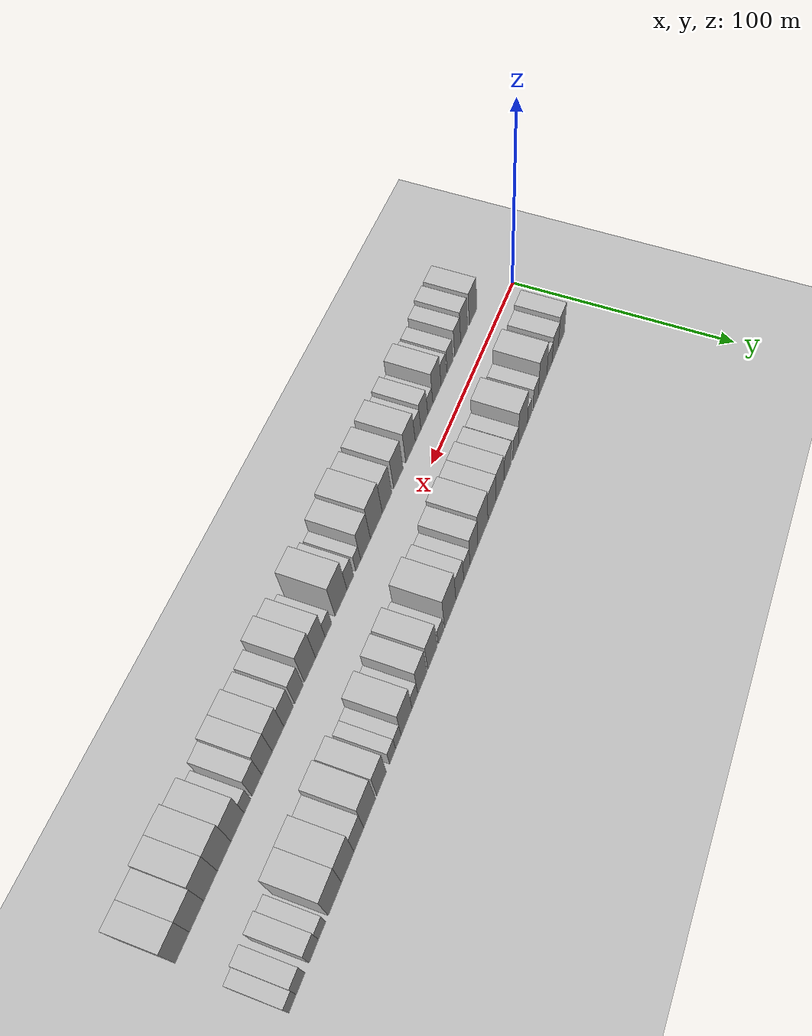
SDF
<?xml version="1.0" encoding="utf-8"?>

<sdf version="1.6">

   <world name="default">

      <gui fullscreen="0">

         <camera name="user_camera">

            <pose>-15 0 4.57585 0 0 0</pose>

            <view_controller>orbit</view_controller>

         </camera>

      </gui>

      <scene>

         <sky>

           <clouds>

             <speed>12</speed>

           </clouds>

         </sky>

         <ambient>0.4 0.4 0.4 1</ambient>

         <background>0.7 0.7 0.7 1</background>

         <shadows>1</shadows>

      </scene>

      <gravity>0 0 -9.8066</gravity>

      <magnetic_field>6e-06 2.3e-05 -4.2e-05</magnetic_field>

      <physics default="0" name="default_physics" type="ode">

         <ode>

            <solver>

               <type>quick</type>

               <iters>10</iters>

               <sor>1.0</sor>

               <use_dynamic_moi_rescaling>0</use_dynamic_moi_rescaling>

            </solver>

            <constraints>

               <cfm>0</cfm>

               <erp>0.2</erp>

               <contact_max_correcting_vel>100</contact_max_correcting_vel>

               <contact_surface_layer>0.001</contact_surface_layer>

            </constraints>

         </ode>

         <max_step_size>0.004</max_step_size>

         <real_time_factor>1</real_time_factor>

         <real_time_update_rate>250</real_time_update_rate>

      </physics>

      <light name="sun" type="directional">

         <cast_shadows>1</cast_shadows>

         <pose>0 0 10 0 0 0</pose>

         <diffuse>0.8 0.8 0.8 1</diffuse>

         <specular>0.2 0.2 0.2 1</specular>

         <attenuation>

            <range>1000</range>

            <constant>0.9</constant>

            <linear>0.01</linear>

            <quadratic>0.001</quadratic>

         </attenuation>

         <direction>-0.5 0.1 -0.9</direction>

      </light>

      <include>

         <name>ground_plane_1</name>

         <uri>model://HANNAS_ground_plane</uri>

         <pose>0 0 0  0 0 0</pose>

      </include>

      <include>

         <name>ground_plane_2</name>

         <uri>model://HANNAS_ground_plane</uri>

         <pose>100 0 0  0 0 0</pose>

      </include>

      <model name="building_1">

         <static>1</static>

         <pose frame="">24.3117 20.0000 0 0.000000 0.000000 1.570796</pose>

         <link name="link">

            <pose frame="">0 0 10.50 0 0 0</pose>

            <collision name="collision">

               <geometry>

                  <box>

                     <size>20.0000 8.6234 21.0000</size>

                  </box>

               </geometry>

               <max_contacts>10</max_contacts>

               <surface>

                  <contact>

                     <ode/>

                  </contact>

                  <bounce/>

                  <friction>

                     <torsional>

                        <ode/>

                     </torsional>

                     <ode/>

                  </friction>

               </surface>

            </collision>

            <visual name="visual">

               <cast_shadows>0</cast_shadows>

               <geometry>

                  <box>

                     <size>20.0000 8.6234 21.0000</size>

                  </box>

               </geometry>

               <material>

                  <script>

                     <uri>model://HANNAS_wall/materials/scripts</uri>

                     <uri>model://HANNAS_wall/materials/textures</uri>

                     <name>vrc/HANNAS_wall</name>

                  </script>

               </material>

            </visual>

            <self_collide>0</self_collide>

            <enable_wind>0</enable_wind>

            <kinematic>0</kinematic>

         </link>

      </model>

      <model name="building_2">

         <static>1</static>

         <pose frame="">32.9170 20.0000 0 0.000000 0.000000 1.570796</pose>

         <link name="link">

            <pose frame="">0 0 9.00 0 0 0</pose>

            <collision name="collision">

               <geometry>

                  <box>

                     <size>20.0000 8.5872 18.0000</size>

                  </box>

               </geometry>

               <max_contacts>10</max_contacts>

               <surface>

                  <contact>

                     <ode/>

                  </contact>

                  <bounce/>

                  <friction>

                     <torsional>

                        <ode/>

                     </torsional>

                     <ode/>

                  </friction>

               </surface>

            </collision>

            <visual name="visual">

               <cast_shadows>0</cast_shadows>

               <geometry>

                  <box>

                     <size>20.0000 8.5872 18.0000</size>

                  </box>

               </geometry>

               <material>

                  <script>

                     <uri>model://HANNAS_wall/materials/scripts</uri>

                     <uri>model://HANNAS_wall/materials/textures</uri>

                     <name>vrc/HANNAS_wall</name>

                  </script>

               </material>

            </visual>

            <self_collide>0</self_collide>

            <enable_wind>0</enable_wind>

            <kinematic>0</kinematic>

         </link>

      </model>

      <model name="building_3">

         <static>1</static>

         <pose frame="">40.7467 20.0000 0 0.000000 0.000000 1.570796</pose>

         <link name="link">

            <pose frame="">0 0 7.50 0 0 0</pose>

            <collision name="collision">

               <geometry>

                  <box>

                     <size>20.0000 7.0722 15.0000</size>

                  </box>

               </geometry>

               <max_contacts>10</max_contacts>

               <surface>

                  <contact>

                     <ode/>

                  </contact>

                  <bounce/>

                  <friction>

                     <torsional>

                        <ode/>

                     </torsional>

                     <ode/>

                  </friction>

               </surface>

            </collision>

            <visual name="visual">

               <cast_shadows>0</cast_shadows>

               <geometry>

                  <box>

                     <size>20.0000 7.0722 15.0000</size>

                  </box>

               </geometry>

               <material>

                  <script>

                     <uri>model://HANNAS_wall/materials/scripts</uri>

                     <uri>model://HANNAS_wall/materials/textures</uri>

                     <name>vrc/HANNAS_wall</name>

                  </script>

               </material>

            </visual>

            <self_collide>0</self_collide>

            <enable_wind>0</enable_wind>

            <kinematic>0</kinematic>

         </link>

      </model>

      <model name="building_4">

         <static>1</static>

         <pose frame="">49.9122 20.0000 0 0.000000 0.000000 1.570796</pose>

         <link name="link">

            <pose frame="">0 0 12.00 0 0 0</pose>

            <collision name="collision">

               <geometry>

                  <box>

                     <size>20.0000 11.2589 24.0000</size>

                  </box>

               </geometry>

               <max_contacts>10</max_contacts>

               <surface>

                  <contact>

                     <ode/>

                  </contact>

                  <bounce/>

                  <friction>

                     <torsional>

                        <ode/>

                     </torsional>

                     <ode/>

                  </friction>

               </surface>

            </collision>

            <visual name="visual">

               <cast_shadows>0</cast_shadows>

               <geometry>

                  <box>

                     <size>20.0000 11.2589 24.0000</size>

                  </box>

               </geometry>

               <material>

                  <script>

                     <uri>model://HANNAS_wall/materials/scripts</uri>

                     <uri>model://HANNAS_wall/materials/textures</uri>

                     <name>vrc/HANNAS_wall</name>

                  </script>

               </material>

            </visual>

            <self_collide>0</self_collide>

            <enable_wind>0</enable_wind>

            <kinematic>0</kinematic>

         </link>

      </model>

      <model name="building_5">

         <static>1</static>

         <pose frame="">59.0413 20.0000 0 0.000000 0.000000 1.570796</pose>

         <link name="link">

            <pose frame="">0 0 7.50 0 0 0</pose>

            <collision name="collision">

               <geometry>

                  <box>

                     <size>20.0000 6.9991 15.0000</size>

                  </box>

               </geometry>

               <max_contacts>10</max_contacts>

               <surface>

                  <contact>

                     <ode/>

                  </contact>

                  <bounce/>

                  <friction>

                     <torsional>

                        <ode/>

                     </torsional>

                     <ode/>

                  </friction>

               </surface>

            </collision>

            <visual name="visual">

               <cast_shadows>0</cast_shadows>

               <geometry>

                  <box>

                     <size>20.0000 6.9991 15.0000</size>

                  </box>

               </geometry>

               <material>

                  <script>

                     <uri>model://HANNAS_wall/materials/scripts</uri>

                     <uri>model://HANNAS_wall/materials/textures</uri>

                     <name>vrc/HANNAS_wall</name>

                  </script>

               </material>

            </visual>

            <self_collide>0</self_collide>

            <enable_wind>0</enable_wind>

            <kinematic>0</kinematic>

         </link>

      </model>

      <model name="building_6">

         <static>1</static>

         <pose frame="">67.0757 20.0000 0 0.000000 0.000000 1.570796</pose>

         <link name="link">

            <pose frame="">0 0 6.00 0 0 0</pose>

            <collision name="collision">

               <geometry>

                  <box>

                     <size>20.0000 5.0698 12.0000</size>

                  </box>

               </geometry>

               <max_contacts>10</max_contacts>

               <surface>

                  <contact>

                     <ode/>

                  </contact>

                  <bounce/>

                  <friction>

                     <torsional>

                        <ode/>

                     </torsional>

                     <ode/>

                  </friction>

               </surface>

            </collision>

            <visual name="visual">

               <cast_shadows>0</cast_shadows>

               <geometry>

                  <box>

                     <size>20.0000 5.0698 12.0000</size>

                  </box>

               </geometry>

               <material>

                  <script>

                     <uri>model://HANNAS_wall/materials/scripts</uri>

                     <uri>model://HANNAS_wall/materials/textures</uri>

                     <name>vrc/HANNAS_wall</name>

                  </script>

               </material>

            </visual>

            <self_collide>0</self_collide>

            <enable_wind>0</enable_wind>

            <kinematic>0</kinematic>

         </link>

      </model>

      <model name="building_7">

         <static>1</static>

         <pose frame="">75.3780 20.0000 0 0.000000 0.000000 1.570796</pose>

         <link name="link">

            <pose frame="">0 0 12.00 0 0 0</pose>

            <collision name="collision">

               <geometry>

                  <box>

                     <size>20.0000 11.5348 24.0000</size>

                  </box>

               </geometry>

               <max_contacts>10</max_contacts>

               <surface>

                  <contact>

                     <ode/>

                  </contact>

                  <bounce/>

                  <friction>

                     <torsional>

                        <ode/>

                     </torsional>

                     <ode/>

                  </friction>

               </surface>

            </collision>

            <visual name="visual">

               <cast_shadows>0</cast_shadows>

               <geometry>

                  <box>

                     <size>20.0000 11.5348 24.0000</size>

                  </box>

               </geometry>

               <material>

                  <script>

                     <uri>model://HANNAS_wall/materials/scripts</uri>

                     <uri>model://HANNAS_wall/materials/textures</uri>

                     <name>vrc/HANNAS_wall</name>

                  </script>

               </material>

            </visual>

            <self_collide>0</self_collide>

            <enable_wind>0</enable_wind>

            <kinematic>0</kinematic>

         </link>

      </model>

      <model name="building_8">

         <static>1</static>

         <pose frame="">84.5590 20.0000 0 0.000000 0.000000 1.570796</pose>

         <link name="link">

            <pose frame="">0 0 7.50 0 0 0</pose>

            <collision name="collision">

               <geometry>

                  <box>

                     <size>20.0000 6.8272 15.0000</size>

                  </box>

               </geometry>

               <max_contacts>10</max_contacts>

               <surface>

                  <contact>

                     <ode/>

                  </contact>

                  <bounce/>

                  <friction>

                     <torsional>

                        <ode/>

                     </torsional>

                     <ode/>

                  </friction>

               </surface>

            </collision>

            <visual name="visual">

               <cast_shadows>0</cast_shadows>

               <geometry>

                  <box>

                     <size>20.0000 6.8272 15.0000</size>

                  </box>

               </geometry>

               <material>

                  <script>

                     <uri>model://HANNAS_wall/materials/scripts</uri>

                     <uri>model://HANNAS_wall/materials/textures</uri>

                     <name>vrc/HANNAS_wall</name>

                  </script>

               </material>

            </visual>

            <self_collide>0</self_collide>

            <enable_wind>0</enable_wind>

            <kinematic>0</kinematic>

         </link>

      </model>

      <model name="building_9">

         <static>1</static>

         <pose frame="">94.1099 20.0000 0 0.000000 0.000000 1.570796</pose>

         <link name="link">

            <pose frame="">0 0 9.00 0 0 0</pose>

            <collision name="collision">

               <geometry>

                  <box>

                     <size>20.0000 8.2747 18.0000</size>

                  </box>

               </geometry>

               <max_contacts>10</max_contacts>

               <surface>

                  <contact>

                     <ode/>

                  </contact>

                  <bounce/>

                  <friction>

                     <torsional>

                        <ode/>

                     </torsional>

                     <ode/>

                  </friction>

               </surface>

            </collision>

            <visual name="visual">

               <cast_shadows>0</cast_shadows>

               <geometry>

                  <box>

                     <size>20.0000 8.2747 18.0000</size>

                  </box>

               </geometry>

               <material>

                  <script>

                     <uri>model://HANNAS_wall/materials/scripts</uri>

                     <uri>model://HANNAS_wall/materials/textures</uri>

                     <name>vrc/HANNAS_wall</name>

                  </script>

               </material>

            </visual>

            <self_collide>0</self_collide>

            <enable_wind>0</enable_wind>

            <kinematic>0</kinematic>

         </link>

      </model>

      <model name="building_10">

         <static>1</static>

         <pose frame="">103.6849 20.0000 0 0.000000 0.000000 1.570796</pose>

         <link name="link">

            <pose frame="">0 0 10.50 0 0 0</pose>

            <collision name="collision">

               <geometry>

                  <box>

                     <size>20.0000 8.8753 21.0000</size>

                  </box>

               </geometry>

               <max_contacts>10</max_contacts>

               <surface>

                  <contact>

                     <ode/>

                  </contact>

                  <bounce/>

                  <friction>

                     <torsional>

                        <ode/>

                     </torsional>

                     <ode/>

                  </friction>

               </surface>

            </collision>

            <visual name="visual">

               <cast_shadows>0</cast_shadows>

               <geometry>

                  <box>

                     <size>20.0000 8.8753 21.0000</size>

                  </box>

               </geometry>

               <material>

                  <script>

                     <uri>model://HANNAS_wall/materials/scripts</uri>

                     <uri>model://HANNAS_wall/materials/textures</uri>

                     <name>vrc/HANNAS_wall</name>

                  </script>

               </material>

            </visual>

            <self_collide>0</self_collide>

            <enable_wind>0</enable_wind>

            <kinematic>0</kinematic>

         </link>

      </model>

      <model name="building_11">

         <static>1</static>

         <pose frame="">112.8992 20.0000 0 0.000000 0.000000 1.570796</pose>

         <link name="link">

            <pose frame="">0 0 10.50 0 0 0</pose>

            <collision name="collision">

               <geometry>

                  <box>

                     <size>20.0000 9.5532 21.0000</size>

                  </box>

               </geometry>

               <max_contacts>10</max_contacts>

               <surface>

                  <contact>

                     <ode/>

                  </contact>

                  <bounce/>

                  <friction>

                     <torsional>

                        <ode/>

                     </torsional>

                     <ode/>

                  </friction>

               </surface>

            </collision>

            <visual name="visual">

               <cast_shadows>0</cast_shadows>

               <geometry>

                  <box>

                     <size>20.0000 9.5532 21.0000</size>

                  </box>

               </geometry>

               <material>

                  <script>

                     <uri>model://HANNAS_wall/materials/scripts</uri>

                     <uri>model://HANNAS_wall/materials/textures</uri>

                     <name>vrc/HANNAS_wall</name>

                  </script>

               </material>

            </visual>

            <self_collide>0</self_collide>

            <enable_wind>0</enable_wind>

            <kinematic>0</kinematic>

         </link>

      </model>

      <model name="building_12">

         <static>1</static>

         <pose frame="">123.3784 20.0000 0 0.000000 0.000000 1.570796</pose>

         <link name="link">

            <pose frame="">0 0 12.00 0 0 0</pose>

            <collision name="collision">

               <geometry>

                  <box>

                     <size>20.0000 11.4053 24.0000</size>

                  </box>

               </geometry>

               <max_contacts>10</max_contacts>

               <surface>

                  <contact>

                     <ode/>

                  </contact>

                  <bounce/>

                  <friction>

                     <torsional>

                        <ode/>

                     </torsional>

                     <ode/>

                  </friction>

               </surface>

            </collision>

            <visual name="visual">

               <cast_shadows>0</cast_shadows>

               <geometry>

                  <box>

                     <size>20.0000 11.4053 24.0000</size>

                  </box>

               </geometry>

               <material>

                  <script>

                     <uri>model://HANNAS_wall/materials/scripts</uri>

                     <uri>model://HANNAS_wall/materials/textures</uri>

                     <name>vrc/HANNAS_wall</name>

                  </script>

               </material>

            </visual>

            <self_collide>0</self_collide>

            <enable_wind>0</enable_wind>

            <kinematic>0</kinematic>

         </link>

      </model>

      <model name="building_13">

         <static>1</static>

         <pose frame="">133.4940 20.0000 0 0.000000 0.000000 1.570796</pose>

         <link name="link">

            <pose frame="">0 0 10.50 0 0 0</pose>

            <collision name="collision">

               <geometry>

                  <box>

                     <size>20.0000 8.8259 21.0000</size>

                  </box>

               </geometry>

               <max_contacts>10</max_contacts>

               <surface>

                  <contact>

                     <ode/>

                  </contact>

                  <bounce/>

                  <friction>

                     <torsional>

                        <ode/>

                     </torsional>

                     <ode/>

                  </friction>

               </surface>

            </collision>

            <visual name="visual">

               <cast_shadows>0</cast_shadows>

               <geometry>

                  <box>

                     <size>20.0000 8.8259 21.0000</size>

                  </box>

               </geometry>

               <material>

                  <script>

                     <uri>model://HANNAS_wall/materials/scripts</uri>

                     <uri>model://HANNAS_wall/materials/textures</uri>

                     <name>vrc/HANNAS_wall</name>

                  </script>

               </material>

            </visual>

            <self_collide>0</self_collide>

            <enable_wind>0</enable_wind>

            <kinematic>0</kinematic>

         </link>

      </model>

      <model name="building_14">

         <static>1</static>

         <pose frame="">141.2551 20.0000 0 0.000000 0.000000 1.570796</pose>

         <link name="link">

            <pose frame="">0 0 7.50 0 0 0</pose>

            <collision name="collision">

               <geometry>

                  <box>

                     <size>20.0000 6.6962 15.0000</size>

                  </box>

               </geometry>

               <max_contacts>10</max_contacts>

               <surface>

                  <contact>

                     <ode/>

                  </contact>

                  <bounce/>

                  <friction>

                     <torsional>

                        <ode/>

                     </torsional>

                     <ode/>

                  </friction>

               </surface>

            </collision>

            <visual name="visual">

               <cast_shadows>0</cast_shadows>

               <geometry>

                  <box>

                     <size>20.0000 6.6962 15.0000</size>

                  </box>

               </geometry>

               <material>

                  <script>

                     <uri>model://HANNAS_wall/materials/scripts</uri>

                     <uri>model://HANNAS_wall/materials/textures</uri>

                     <name>vrc/HANNAS_wall</name>

                  </script>

               </material>

            </visual>

            <self_collide>0</self_collide>

            <enable_wind>0</enable_wind>

            <kinematic>0</kinematic>

         </link>

      </model>

      <model name="building_15">

         <static>1</static>

         <pose frame="">148.8612 20.0000 0 0.000000 0.000000 1.570796</pose>

         <link name="link">

            <pose frame="">0 0 9.00 0 0 0</pose>

            <collision name="collision">

               <geometry>

                  <box>

                     <size>20.0000 8.5161 18.0000</size>

                  </box>

               </geometry>

               <max_contacts>10</max_contacts>

               <surface>

                  <contact>

                     <ode/>

                  </contact>

                  <bounce/>

                  <friction>

                     <torsional>

                        <ode/>

                     </torsional>

                     <ode/>

                  </friction>

               </surface>

            </collision>

            <visual name="visual">

               <cast_shadows>0</cast_shadows>

               <geometry>

                  <box>

                     <size>20.0000 8.5161 18.0000</size>

                  </box>

               </geometry>

               <material>

                  <script>

                     <uri>model://HANNAS_wall/materials/scripts</uri>

                     <uri>model://HANNAS_wall/materials/textures</uri>

                     <name>vrc/HANNAS_wall</name>

                  </script>

               </material>

            </visual>

            <self_collide>0</self_collide>

            <enable_wind>0</enable_wind>

            <kinematic>0</kinematic>

         </link>

      </model>

      <model name="building_16">

         <static>1</static>

         <pose frame="">159.0766 20.0000 0 0.000000 0.000000 1.570796</pose>

         <link name="link">

            <pose frame="">0 0 12.00 0 0 0</pose>

            <collision name="collision">

               <geometry>

                  <box>

                     <size>20.0000 11.9148 24.0000</size>

                  </box>

               </geometry>

               <max_contacts>10</max_contacts>

               <surface>

                  <contact>

                     <ode/>

                  </contact>

                  <bounce/>

                  <friction>

                     <torsional>

                        <ode/>

                     </torsional>

                     <ode/>

                  </friction>

               </surface>

            </collision>

            <visual name="visual">

               <cast_shadows>0</cast_shadows>

               <geometry>

                  <box>

                     <size>20.0000 11.9148 24.0000</size>

                  </box>

               </geometry>

               <material>

                  <script>

                     <uri>model://HANNAS_wall/materials/scripts</uri>

                     <uri>model://HANNAS_wall/materials/textures</uri>

                     <name>vrc/HANNAS_wall</name>

                  </script>

               </material>

            </visual>

            <self_collide>0</self_collide>

            <enable_wind>0</enable_wind>

            <kinematic>0</kinematic>

         </link>

      </model>

      <model name="building_17">

         <static>1</static>

         <pose frame="">168.8202 20.0000 0 0.000000 0.000000 1.570796</pose>

         <link name="link">

            <pose frame="">0 0 6.00 0 0 0</pose>

            <collision name="collision">

               <geometry>

                  <box>

                     <size>20.0000 5.5725 12.0000</size>

                  </box>

               </geometry>

               <max_contacts>10</max_contacts>

               <surface>

                  <contact>

                     <ode/>

                  </contact>

                  <bounce/>

                  <friction>

                     <torsional>

                        <ode/>

                     </torsional>

                     <ode/>

                  </friction>

               </surface>

            </collision>

            <visual name="visual">

               <cast_shadows>0</cast_shadows>

               <geometry>

                  <box>

                     <size>20.0000 5.5725 12.0000</size>

                  </box>

               </geometry>

               <material>

                  <script>

                     <uri>model://HANNAS_wall/materials/scripts</uri>

                     <uri>model://HANNAS_wall/materials/textures</uri>

                     <name>vrc/HANNAS_wall</name>

                  </script>

               </material>

            </visual>

            <self_collide>0</self_collide>

            <enable_wind>0</enable_wind>

            <kinematic>0</kinematic>

         </link>

      </model>

      <model name="building_18">

         <static>1</static>

         <pose frame="">177.3707 20.0000 0 0.000000 0.000000 1.570796</pose>

         <link name="link">

            <pose frame="">0 0 10.50 0 0 0</pose>

            <collision name="collision">

               <geometry>

                  <box>

                     <size>20.0000 9.5284 21.0000</size>

                  </box>

               </geometry>

               <max_contacts>10</max_contacts>

               <surface>

                  <contact>

                     <ode/>

                  </contact>

                  <bounce/>

                  <friction>

                     <torsional>

                        <ode/>

                     </torsional>

                     <ode/>

                  </friction>

               </surface>

            </collision>

            <visual name="visual">

               <cast_shadows>0</cast_shadows>

               <geometry>

                  <box>

                     <size>20.0000 9.5284 21.0000</size>

                  </box>

               </geometry>

               <material>

                  <script>

                     <uri>model://HANNAS_wall/materials/scripts</uri>

                     <uri>model://HANNAS_wall/materials/textures</uri>

                     <name>vrc/HANNAS_wall</name>

                  </script>

               </material>

            </visual>

            <self_collide>0</self_collide>

            <enable_wind>0</enable_wind>

            <kinematic>0</kinematic>

         </link>

      </model>

      <model name="building_19">

         <static>1</static>

         <pose frame="">187.5096 20.0000 0 0.000000 0.000000 1.570796</pose>

         <link name="link">

            <pose frame="">0 0 10.50 0 0 0</pose>

            <collision name="collision">

               <geometry>

                  <box>

                     <size>20.0000 8.7494 21.0000</size>

                  </box>

               </geometry>

               <max_contacts>10</max_contacts>

               <surface>

                  <contact>

                     <ode/>

                  </contact>

                  <bounce/>

                  <friction>

                     <torsional>

                        <ode/>

                     </torsional>

                     <ode/>

                  </friction>

               </surface>

            </collision>

            <visual name="visual">

               <cast_shadows>0</cast_shadows>

               <geometry>

                  <box>

                     <size>20.0000 8.7494 21.0000</size>

                  </box>

               </geometry>

               <material>

                  <script>

                     <uri>model://HANNAS_wall/materials/scripts</uri>

                     <uri>model://HANNAS_wall/materials/textures</uri>

                     <name>vrc/HANNAS_wall</name>

                  </script>

               </material>

            </visual>

            <self_collide>0</self_collide>

            <enable_wind>0</enable_wind>

            <kinematic>0</kinematic>

         </link>

      </model>

      <model name="building_20">

         <static>1</static>

         <pose frame="">194.7217 20.0000 0 0.000000 0.000000 1.570796</pose>

         <link name="link">

            <pose frame="">0 0 6.00 0 0 0</pose>

            <collision name="collision">

               <geometry>

                  <box>

                     <size>20.0000 5.6749 12.0000</size>

                  </box>

               </geometry>

               <max_contacts>10</max_contacts>

               <surface>

                  <contact>

                     <ode/>

                  </contact>

                  <bounce/>

                  <friction>

                     <torsional>

                        <ode/>

                     </torsional>

                     <ode/>

                  </friction>

               </surface>

            </collision>

            <visual name="visual">

               <cast_shadows>0</cast_shadows>

               <geometry>

                  <box>

                     <size>20.0000 5.6749 12.0000</size>

                  </box>

               </geometry>

               <material>

                  <script>

                     <uri>model://HANNAS_wall/materials/scripts</uri>

                     <uri>model://HANNAS_wall/materials/textures</uri>

                     <name>vrc/HANNAS_wall</name>

                  </script>

               </material>

            </visual>

            <self_collide>0</self_collide>

            <enable_wind>0</enable_wind>

            <kinematic>0</kinematic>

         </link>

      </model>

      <model name="building_21">

         <static>1</static>

         <pose frame="">202.7160 20.0000 0 0.000000 0.000000 1.570796</pose>

         <link name="link">

            <pose frame="">0 0 10.50 0 0 0</pose>

            <collision name="collision">

               <geometry>

                  <box>

                     <size>20.0000 10.3136 21.0000</size>

                  </box>

               </geometry>

               <max_contacts>10</max_contacts>

               <surface>

                  <contact>

                     <ode/>

                  </contact>

                  <bounce/>

                  <friction>

                     <torsional>

                        <ode/>

                     </torsional>

                     <ode/>

                  </friction>

               </surface>

            </collision>

            <visual name="visual">

               <cast_shadows>0</cast_shadows>

               <geometry>

                  <box>

                     <size>20.0000 10.3136 21.0000</size>

                  </box>

               </geometry>

               <material>

                  <script>

                     <uri>model://HANNAS_wall/materials/scripts</uri>

                     <uri>model://HANNAS_wall/materials/textures</uri>

                     <name>vrc/HANNAS_wall</name>

                  </script>

               </material>

            </visual>

            <self_collide>0</self_collide>

            <enable_wind>0</enable_wind>

            <kinematic>0</kinematic>

         </link>

      </model>

      <model name="building_22">

         <static>1</static>

         <pose frame="">210.4509 20.0000 0 0.000000 0.000000 1.570796</pose>

         <link name="link">

            <pose frame="">0 0 6.00 0 0 0</pose>

            <collision name="collision">

               <geometry>

                  <box>

                     <size>20.0000 5.1561 12.0000</size>

                  </box>

               </geometry>

               <max_contacts>10</max_contacts>

               <surface>

                  <contact>

                     <ode/>

                  </contact>

                  <bounce/>

                  <friction>

                     <torsional>

                        <ode/>

                     </torsional>

                     <ode/>

                  </friction>

               </surface>

            </collision>

            <visual name="visual">

               <cast_shadows>0</cast_shadows>

               <geometry>

                  <box>

                     <size>20.0000 5.1561 12.0000</size>

                  </box>

               </geometry>

               <material>

                  <script>

                     <uri>model://HANNAS_wall/materials/scripts</uri>

                     <uri>model://HANNAS_wall/materials/textures</uri>

                     <name>vrc/HANNAS_wall</name>

                  </script>

               </material>

            </visual>

            <self_collide>0</self_collide>

            <enable_wind>0</enable_wind>

            <kinematic>0</kinematic>

         </link>

      </model>

      <model name="building_23">

         <static>1</static>

         <pose frame="">215.7773 20.0000 0 0.000000 0.000000 1.570796</pose>

         <link name="link">

            <pose frame="">0 0 6.00 0 0 0</pose>

            <collision name="collision">

               <geometry>

                  <box>

                     <size>20.0000 5.4966 12.0000</size>

                  </box>

               </geometry>

               <max_contacts>10</max_contacts>

               <surface>

                  <contact>

                     <ode/>

                  </contact>

                  <bounce/>

                  <friction>

                     <torsional>

                        <ode/>

                     </torsional>

                     <ode/>

                  </friction>

               </surface>

            </collision>

            <visual name="visual">

               <cast_shadows>0</cast_shadows>

               <geometry>

                  <box>

                     <size>20.0000 5.4966 12.0000</size>

                  </box>

               </geometry>

               <material>

                  <script>

                     <uri>model://HANNAS_wall/materials/scripts</uri>

                     <uri>model://HANNAS_wall/materials/textures</uri>

                     <name>vrc/HANNAS_wall</name>

                  </script>

               </material>

            </visual>

            <self_collide>0</self_collide>

            <enable_wind>0</enable_wind>

            <kinematic>0</kinematic>

         </link>

      </model>

      <model name="building_24">

         <static>1</static>

         <pose frame="">225.8295 20.0000 0 0.000000 0.000000 1.570796</pose>

         <link name="link">

            <pose frame="">0 0 10.50 0 0 0</pose>

            <collision name="collision">

               <geometry>

                  <box>

                     <size>20.0000 8.6078 21.0000</size>

                  </box>

               </geometry>

               <max_contacts>10</max_contacts>

               <surface>

                  <contact>

                     <ode/>

                  </contact>

                  <bounce/>

                  <friction>

                     <torsional>

                        <ode/>

                     </torsional>

                     <ode/>

                  </friction>

               </surface>

            </collision>

            <visual name="visual">

               <cast_shadows>0</cast_shadows>

               <geometry>

                  <box>

                     <size>20.0000 8.6078 21.0000</size>

                  </box>

               </geometry>

               <material>

                  <script>

                     <uri>model://HANNAS_wall/materials/scripts</uri>

                     <uri>model://HANNAS_wall/materials/textures</uri>

                     <name>vrc/HANNAS_wall</name>

                  </script>

               </material>

            </visual>

            <self_collide>0</self_collide>

            <enable_wind>0</enable_wind>

            <kinematic>0</kinematic>

         </link>

      </model>

      <model name="building_25">

         <static>1</static>

         <pose frame="">236.2986 20.0000 0 0.000000 0.000000 1.570796</pose>

         <link name="link">

            <pose frame="">0 0 12.00 0 0 0</pose>

            <collision name="collision">

               <geometry>

                  <box>

                     <size>20.0000 10.3304 24.0000</size>

                  </box>

               </geometry>

               <max_contacts>10</max_contacts>

               <surface>

                  <contact>

                     <ode/>

                  </contact>

                  <bounce/>

                  <friction>

                     <torsional>

                        <ode/>

                     </torsional>

                     <ode/>

                  </friction>

               </surface>

            </collision>

            <visual name="visual">

               <cast_shadows>0</cast_shadows>

               <geometry>

                  <box>

                     <size>20.0000 10.3304 24.0000</size>

                  </box>

               </geometry>

               <material>

                  <script>

                     <uri>model://HANNAS_wall/materials/scripts</uri>

                     <uri>model://HANNAS_wall/materials/textures</uri>

                     <name>vrc/HANNAS_wall</name>

                  </script>

               </material>

            </visual>

            <self_collide>0</self_collide>

            <enable_wind>0</enable_wind>

            <kinematic>0</kinematic>

         </link>

      </model>

      <model name="building_26">

         <static>1</static>

         <pose frame="">245.6230 20.0000 0 0.000000 0.000000 1.570796</pose>

         <link name="link">

            <pose frame="">0 0 9.00 0 0 0</pose>

            <collision name="collision">

               <geometry>

                  <box>

                     <size>20.0000 8.3184 18.0000</size>

                  </box>

               </geometry>

               <max_contacts>10</max_contacts>

               <surface>

                  <contact>

                     <ode/>

                  </contact>

                  <bounce/>

                  <friction>

                     <torsional>

                        <ode/>

                     </torsional>

                     <ode/>

                  </friction>

               </surface>

            </collision>

            <visual name="visual">

               <cast_shadows>0</cast_shadows>

               <geometry>

                  <box>

                     <size>20.0000 8.3184 18.0000</size>

                  </box>

               </geometry>

               <material>

                  <script>

                     <uri>model://HANNAS_wall/materials/scripts</uri>

                     <uri>model://HANNAS_wall/materials/textures</uri>

                     <name>vrc/HANNAS_wall</name>

                  </script>

               </material>

            </visual>

            <self_collide>0</self_collide>

            <enable_wind>0</enable_wind>

            <kinematic>0</kinematic>

         </link>

      </model>

      <model name="building_27">

         <static>1</static>

         <pose frame="">254.9688 20.0000 0 0.000000 0.000000 1.570796</pose>

         <link name="link">

            <pose frame="">0 0 12.00 0 0 0</pose>

            <collision name="collision">

               <geometry>

                  <box>

                     <size>20.0000 10.3732 24.0000</size>

                  </box>

               </geometry>

               <max_contacts>10</max_contacts>

               <surface>

                  <contact>

                     <ode/>

                  </contact>

                  <bounce/>

                  <friction>

                     <torsional>

                        <ode/>

                     </torsional>

                     <ode/>

                  </friction>

               </surface>

            </collision>

            <visual name="visual">

               <cast_shadows>0</cast_shadows>

               <geometry>

                  <box>

                     <size>20.0000 10.3732 24.0000</size>

                  </box>

               </geometry>

               <material>

                  <script>

                     <uri>model://HANNAS_wall/materials/scripts</uri>

                     <uri>model://HANNAS_wall/materials/textures</uri>

                     <name>vrc/HANNAS_wall</name>

                  </script>

               </material>

            </visual>

            <self_collide>0</self_collide>

            <enable_wind>0</enable_wind>

            <kinematic>0</kinematic>

         </link>

      </model>

      <model name="building_28">

         <static>1</static>

         <pose frame="">265.5905 20.0000 0 0.000000 0.000000 1.570796</pose>

         <link name="link">

            <pose frame="">0 0 12.00 0 0 0</pose>

            <collision name="collision">

               <geometry>

                  <box>

                     <size>20.0000 10.8702 24.0000</size>

                  </box>

               </geometry>

               <max_contacts>10</max_contacts>

               <surface>

                  <contact>

                     <ode/>

                  </contact>

                  <bounce/>

                  <friction>

                     <torsional>

                        <ode/>

                     </torsional>

                     <ode/>

                  </friction>

               </surface>

            </collision>

            <visual name="visual">

               <cast_shadows>0</cast_shadows>

               <geometry>

                  <box>

                     <size>20.0000 10.8702 24.0000</size>

                  </box>

               </geometry>

               <material>

                  <script>

                     <uri>model://HANNAS_wall/materials/scripts</uri>

                     <uri>model://HANNAS_wall/materials/textures</uri>

                     <name>vrc/HANNAS_wall</name>

                  </script>

               </material>

            </visual>

            <self_collide>0</self_collide>

            <enable_wind>0</enable_wind>

            <kinematic>0</kinematic>

         </link>

      </model>

      <model name="building_29">

         <static>1</static>

         <pose frame="">275.9027 20.0000 0 0.000000 0.000000 1.570796</pose>

         <link name="link">

            <pose frame="">0 0 6.00 0 0 0</pose>

            <collision name="collision">

               <geometry>

                  <box>

                     <size>20.0000 5.7542 12.0000</size>

                  </box>

               </geometry>

               <max_contacts>10</max_contacts>

               <surface>

                  <contact>

                     <ode/>

                  </contact>

                  <bounce/>

                  <friction>

                     <torsional>

                        <ode/>

                     </torsional>

                     <ode/>

                  </friction>

               </surface>

            </collision>

            <visual name="visual">

               <cast_shadows>0</cast_shadows>

               <geometry>

                  <box>

                     <size>20.0000 5.7542 12.0000</size>

                  </box>

               </geometry>

               <material>

                  <script>

                     <uri>model://HANNAS_wall/materials/scripts</uri>

                     <uri>model://HANNAS_wall/materials/textures</uri>

                     <name>vrc/HANNAS_wall</name>

                  </script>

               </material>

            </visual>

            <self_collide>0</self_collide>

            <enable_wind>0</enable_wind>

            <kinematic>0</kinematic>

         </link>

      </model>

      <model name="building_30">

         <static>1</static>

         <pose frame="">282.4254 20.0000 0 0.000000 0.000000 1.570796</pose>

         <link name="link">

            <pose frame="">0 0 7.50 0 0 0</pose>

            <collision name="collision">

               <geometry>

                  <box>

                     <size>20.0000 7.2912 15.0000</size>

                  </box>

               </geometry>

               <max_contacts>10</max_contacts>

               <surface>

                  <contact>

                     <ode/>

                  </contact>

                  <bounce/>

                  <friction>

                     <torsional>

                        <ode/>

                     </torsional>

                     <ode/>

                  </friction>

               </surface>

            </collision>

            <visual name="visual">

               <cast_shadows>0</cast_shadows>

               <geometry>

                  <box>

                     <size>20.0000 7.2912 15.0000</size>

                  </box>

               </geometry>

               <material>

                  <script>

                     <uri>model://HANNAS_wall/materials/scripts</uri>

                     <uri>model://HANNAS_wall/materials/textures</uri>

                     <name>vrc/HANNAS_wall</name>

                  </script>

               </material>

            </visual>

            <self_collide>0</self_collide>

            <enable_wind>0</enable_wind>

            <kinematic>0</kinematic>

         </link>

      </model>

      <model name="building_31">

         <static>1</static>

         <pose frame="">292.4112 20.0000 0 0.000000 0.000000 1.570796</pose>

         <link name="link">

            <pose frame="">0 0 7.50 0 0 0</pose>

            <collision name="collision">

               <geometry>

                  <box>

                     <size>20.0000 6.6804 15.0000</size>

                  </box>

               </geometry>

               <max_contacts>10</max_contacts>

               <surface>

                  <contact>

                     <ode/>

                  </contact>

                  <bounce/>

                  <friction>

                     <torsional>

                        <ode/>

                     </torsional>

                     <ode/>

                  </friction>

               </surface>

            </collision>

            <visual name="visual">

               <cast_shadows>0</cast_shadows>

               <geometry>

                  <box>

                     <size>20.0000 6.6804 15.0000</size>

                  </box>

               </geometry>

               <material>

                  <script>

                     <uri>model://HANNAS_wall/materials/scripts</uri>

                     <uri>model://HANNAS_wall/materials/textures</uri>

                     <name>vrc/HANNAS_wall</name>

                  </script>

               </material>

            </visual>

            <self_collide>0</self_collide>

            <enable_wind>0</enable_wind>

            <kinematic>0</kinematic>

         </link>

      </model>

      <model name="building_32">

         <static>1</static>

         <pose frame="">298.5404 20.0000 0 0.000000 0.000000 1.570796</pose>

         <link name="link">

            <pose frame="">0 0 6.00 0 0 0</pose>

            <collision name="collision">

               <geometry>

                  <box>

                     <size>20.0000 5.5781 12.0000</size>

                  </box>

               </geometry>

               <max_contacts>10</max_contacts>

               <surface>

                  <contact>

                     <ode/>

                  </contact>

                  <bounce/>

                  <friction>

                     <torsional>

                        <ode/>

                     </torsional>

                     <ode/>

                  </friction>

               </surface>

            </collision>

            <visual name="visual">

               <cast_shadows>0</cast_shadows>

               <geometry>

                  <box>

                     <size>20.0000 5.5781 12.0000</size>

                  </box>

               </geometry>

               <material>

                  <script>

                     <uri>model://HANNAS_wall/materials/scripts</uri>

                     <uri>model://HANNAS_wall/materials/textures</uri>

                     <name>vrc/HANNAS_wall</name>

                  </script>

               </material>

            </visual>

            <self_collide>0</self_collide>

            <enable_wind>0</enable_wind>

            <kinematic>0</kinematic>

         </link>

      </model>

      <model name="building_33">

         <static>1</static>

         <pose frame="">24.8160 -20.0000 0 0.000000 0.000000 1.570796</pose>

         <link name="link">

            <pose frame="">0 0 10.50 0 0 0</pose>

            <collision name="collision">

               <geometry>

                  <box>

                     <size>20.0000 9.6321 21.0000</size>

                  </box>

               </geometry>

               <max_contacts>10</max_contacts>

               <surface>

                  <contact>

                     <ode/>

                  </contact>

                  <bounce/>

                  <friction>

                     <torsional>

                        <ode/>

                     </torsional>

                     <ode/>

                  </friction>

               </surface>

            </collision>

            <visual name="visual">

               <cast_shadows>0</cast_shadows>

               <geometry>

                  <box>

                     <size>20.0000 9.6321 21.0000</size>

                  </box>

               </geometry>

               <material>

                  <script>

                     <uri>model://HANNAS_wall/materials/scripts</uri>

                     <uri>model://HANNAS_wall/materials/textures</uri>

                     <name>vrc/HANNAS_wall</name>

                  </script>

               </material>

            </visual>

            <self_collide>0</self_collide>

            <enable_wind>0</enable_wind>

            <kinematic>0</kinematic>

         </link>

      </model>

      <model name="building_34">

         <static>1</static>

         <pose frame="">35.8480 -20.0000 0 0.000000 0.000000 1.570796</pose>

         <link name="link">

            <pose frame="">0 0 10.50 0 0 0</pose>

            <collision name="collision">

               <geometry>

                  <box>

                     <size>20.0000 8.4320 21.0000</size>

                  </box>

               </geometry>

               <max_contacts>10</max_contacts>

               <surface>

                  <contact>

                     <ode/>

                  </contact>

                  <bounce/>

                  <friction>

                     <torsional>

                        <ode/>

                     </torsional>

                     <ode/>

                  </friction>

               </surface>

            </collision>

            <visual name="visual">

               <cast_shadows>0</cast_shadows>

               <geometry>

                  <box>

                     <size>20.0000 8.4320 21.0000</size>

                  </box>

               </geometry>

               <material>

                  <script>

                     <uri>model://HANNAS_wall/materials/scripts</uri>

                     <uri>model://HANNAS_wall/materials/textures</uri>

                     <name>vrc/HANNAS_wall</name>

                  </script>

               </material>

            </visual>

            <self_collide>0</self_collide>

            <enable_wind>0</enable_wind>

            <kinematic>0</kinematic>

         </link>

      </model>

      <model name="building_35">

         <static>1</static>

         <pose frame="">43.8123 -20.0000 0 0.000000 0.000000 1.570796</pose>

         <link name="link">

            <pose frame="">0 0 9.00 0 0 0</pose>

            <collision name="collision">

               <geometry>

                  <box>

                     <size>20.0000 7.4966 18.0000</size>

                  </box>

               </geometry>

               <max_contacts>10</max_contacts>

               <surface>

                  <contact>

                     <ode/>

                  </contact>

                  <bounce/>

                  <friction>

                     <torsional>

                        <ode/>

                     </torsional>

                     <ode/>

                  </friction>

               </surface>

            </collision>

            <visual name="visual">

               <cast_shadows>0</cast_shadows>

               <geometry>

                  <box>

                     <size>20.0000 7.4966 18.0000</size>

                  </box>

               </geometry>

               <material>

                  <script>

                     <uri>model://HANNAS_wall/materials/scripts</uri>

                     <uri>model://HANNAS_wall/materials/textures</uri>

                     <name>vrc/HANNAS_wall</name>

                  </script>

               </material>

            </visual>

            <self_collide>0</self_collide>

            <enable_wind>0</enable_wind>

            <kinematic>0</kinematic>

         </link>

      </model>

      <model name="building_36">

         <static>1</static>

         <pose frame="">52.9857 -20.0000 0 0.000000 0.000000 1.570796</pose>

         <link name="link">

            <pose frame="">0 0 7.50 0 0 0</pose>

            <collision name="collision">

               <geometry>

                  <box>

                     <size>20.0000 6.8501 15.0000</size>

                  </box>

               </geometry>

               <max_contacts>10</max_contacts>

               <surface>

                  <contact>

                     <ode/>

                  </contact>

                  <bounce/>

                  <friction>

                     <torsional>

                        <ode/>

                     </torsional>

                     <ode/>

                  </friction>

               </surface>

            </collision>

            <visual name="visual">

               <cast_shadows>0</cast_shadows>

               <geometry>

                  <box>

                     <size>20.0000 6.8501 15.0000</size>

                  </box>

               </geometry>

               <material>

                  <script>

                     <uri>model://HANNAS_wall/materials/scripts</uri>

                     <uri>model://HANNAS_wall/materials/textures</uri>

                     <name>vrc/HANNAS_wall</name>

                  </script>

               </material>

            </visual>

            <self_collide>0</self_collide>

            <enable_wind>0</enable_wind>

            <kinematic>0</kinematic>

         </link>

      </model>

      <model name="building_37">

         <static>1</static>

         <pose frame="">60.5205 -20.0000 0 0.000000 0.000000 1.570796</pose>

         <link name="link">

            <pose frame="">0 0 7.50 0 0 0</pose>

            <collision name="collision">

               <geometry>

                  <box>

                     <size>20.0000 6.2196 15.0000</size>

                  </box>

               </geometry>

               <max_contacts>10</max_contacts>

               <surface>

                  <contact>

                     <ode/>

                  </contact>

                  <bounce/>

                  <friction>

                     <torsional>

                        <ode/>

                     </torsional>

                     <ode/>

                  </friction>

               </surface>

            </collision>

            <visual name="visual">

               <cast_shadows>0</cast_shadows>

               <geometry>

                  <box>

                     <size>20.0000 6.2196 15.0000</size>

                  </box>

               </geometry>

               <material>

                  <script>

                     <uri>model://HANNAS_wall/materials/scripts</uri>

                     <uri>model://HANNAS_wall/materials/textures</uri>

                     <name>vrc/HANNAS_wall</name>

                  </script>

               </material>

            </visual>

            <self_collide>0</self_collide>

            <enable_wind>0</enable_wind>

            <kinematic>0</kinematic>

         </link>

      </model>

      <model name="building_38">

         <static>1</static>

         <pose frame="">68.3613 -20.0000 0 0.000000 0.000000 1.570796</pose>

         <link name="link">

            <pose frame="">0 0 10.50 0 0 0</pose>

            <collision name="collision">

               <geometry>

                  <box>

                     <size>20.0000 9.4619 21.0000</size>

                  </box>

               </geometry>

               <max_contacts>10</max_contacts>

               <surface>

                  <contact>

                     <ode/>

                  </contact>

                  <bounce/>

                  <friction>

                     <torsional>

                        <ode/>

                     </torsional>

                     <ode/>

                  </friction>

               </surface>

            </collision>

            <visual name="visual">

               <cast_shadows>0</cast_shadows>

               <geometry>

                  <box>

                     <size>20.0000 9.4619 21.0000</size>

                  </box>

               </geometry>

               <material>

                  <script>

                     <uri>model://HANNAS_wall/materials/scripts</uri>

                     <uri>model://HANNAS_wall/materials/textures</uri>

                     <name>vrc/HANNAS_wall</name>

                  </script>

               </material>

            </visual>

            <self_collide>0</self_collide>

            <enable_wind>0</enable_wind>

            <kinematic>0</kinematic>

         </link>

      </model>

      <model name="building_39">

         <static>1</static>

         <pose frame="">75.9973 -20.0000 0 0.000000 0.000000 1.570796</pose>

         <link name="link">

            <pose frame="">0 0 6.00 0 0 0</pose>

            <collision name="collision">

               <geometry>

                  <box>

                     <size>20.0000 5.8101 12.0000</size>

                  </box>

               </geometry>

               <max_contacts>10</max_contacts>

               <surface>

                  <contact>

                     <ode/>

                  </contact>

                  <bounce/>

                  <friction>

                     <torsional>

                        <ode/>

                     </torsional>

                     <ode/>

                  </friction>

               </surface>

            </collision>

            <visual name="visual">

               <cast_shadows>0</cast_shadows>

               <geometry>

                  <box>

                     <size>20.0000 5.8101 12.0000</size>

                  </box>

               </geometry>

               <material>

                  <script>

                     <uri>model://HANNAS_wall/materials/scripts</uri>

                     <uri>model://HANNAS_wall/materials/textures</uri>

                     <name>vrc/HANNAS_wall</name>

                  </script>

               </material>

            </visual>

            <self_collide>0</self_collide>

            <enable_wind>0</enable_wind>

            <kinematic>0</kinematic>

         </link>

      </model>

      <model name="building_40">

         <static>1</static>

         <pose frame="">82.7998 -20.0000 0 0.000000 0.000000 1.570796</pose>

         <link name="link">

            <pose frame="">0 0 9.00 0 0 0</pose>

            <collision name="collision">

               <geometry>

                  <box>

                     <size>20.0000 7.7949 18.0000</size>

                  </box>

               </geometry>

               <max_contacts>10</max_contacts>

               <surface>

                  <contact>

                     <ode/>

                  </contact>

                  <bounce/>

                  <friction>

                     <torsional>

                        <ode/>

                     </torsional>

                     <ode/>

                  </friction>

               </surface>

            </collision>

            <visual name="visual">

               <cast_shadows>0</cast_shadows>

               <geometry>

                  <box>

                     <size>20.0000 7.7949 18.0000</size>

                  </box>

               </geometry>

               <material>

                  <script>

                     <uri>model://HANNAS_wall/materials/scripts</uri>

                     <uri>model://HANNAS_wall/materials/textures</uri>

                     <name>vrc/HANNAS_wall</name>

                  </script>

               </material>

            </visual>

            <self_collide>0</self_collide>

            <enable_wind>0</enable_wind>

            <kinematic>0</kinematic>

         </link>

      </model>

      <model name="building_41">

         <static>1</static>

         <pose frame="">89.7791 -20.0000 0 0.000000 0.000000 1.570796</pose>

         <link name="link">

            <pose frame="">0 0 7.50 0 0 0</pose>

            <collision name="collision">

               <geometry>

                  <box>

                     <size>20.0000 6.1637 15.0000</size>

                  </box>

               </geometry>

               <max_contacts>10</max_contacts>

               <surface>

                  <contact>

                     <ode/>

                  </contact>

                  <bounce/>

                  <friction>

                     <torsional>

                        <ode/>

                     </torsional>

                     <ode/>

                  </friction>

               </surface>

            </collision>

            <visual name="visual">

               <cast_shadows>0</cast_shadows>

               <geometry>

                  <box>

                     <size>20.0000 6.1637 15.0000</size>

                  </box>

               </geometry>

               <material>

                  <script>

                     <uri>model://HANNAS_wall/materials/scripts</uri>

                     <uri>model://HANNAS_wall/materials/textures</uri>

                     <name>vrc/HANNAS_wall</name>

                  </script>

               </material>

            </visual>

            <self_collide>0</self_collide>

            <enable_wind>0</enable_wind>

            <kinematic>0</kinematic>

         </link>

      </model>

      <model name="building_42">

         <static>1</static>

         <pose frame="">98.0552 -20.0000 0 0.000000 0.000000 1.570796</pose>

         <link name="link">

            <pose frame="">0 0 10.50 0 0 0</pose>

            <collision name="collision">

               <geometry>

                  <box>

                     <size>20.0000 10.3885 21.0000</size>

                  </box>

               </geometry>

               <max_contacts>10</max_contacts>

               <surface>

                  <contact>

                     <ode/>

                  </contact>

                  <bounce/>

                  <friction>

                     <torsional>

                        <ode/>

                     </torsional>

                     <ode/>

                  </friction>

               </surface>

            </collision>

            <visual name="visual">

               <cast_shadows>0</cast_shadows>

               <geometry>

                  <box>

                     <size>20.0000 10.3885 21.0000</size>

                  </box>

               </geometry>

               <material>

                  <script>

                     <uri>model://HANNAS_wall/materials/scripts</uri>

                     <uri>model://HANNAS_wall/materials/textures</uri>

                     <name>vrc/HANNAS_wall</name>

                  </script>

               </material>

            </visual>

            <self_collide>0</self_collide>

            <enable_wind>0</enable_wind>

            <kinematic>0</kinematic>

         </link>

      </model>

      <model name="building_43">

         <static>1</static>

         <pose frame="">111.2123 -20.0000 0 0.000000 0.000000 1.570796</pose>

         <link name="link">

            <pose frame="">0 0 10.50 0 0 0</pose>

            <collision name="collision">

               <geometry>

                  <box>

                     <size>20.0000 9.9257 21.0000</size>

                  </box>

               </geometry>

               <max_contacts>10</max_contacts>

               <surface>

                  <contact>

                     <ode/>

                  </contact>

                  <bounce/>

                  <friction>

                     <torsional>

                        <ode/>

                     </torsional>

                     <ode/>

                  </friction>

               </surface>

            </collision>

            <visual name="visual">

               <cast_shadows>0</cast_shadows>

               <geometry>

                  <box>

                     <size>20.0000 9.9257 21.0000</size>

                  </box>

               </geometry>

               <material>

                  <script>

                     <uri>model://HANNAS_wall/materials/scripts</uri>

                     <uri>model://HANNAS_wall/materials/textures</uri>

                     <name>vrc/HANNAS_wall</name>

                  </script>

               </material>

            </visual>

            <self_collide>0</self_collide>

            <enable_wind>0</enable_wind>

            <kinematic>0</kinematic>

         </link>

      </model>

      <model name="building_44">

         <static>1</static>

         <pose frame="">123.0410 -20.0000 0 0.000000 0.000000 1.570796</pose>

         <link name="link">

            <pose frame="">0 0 10.50 0 0 0</pose>

            <collision name="collision">

               <geometry>

                  <box>

                     <size>20.0000 9.7318 21.0000</size>

                  </box>

               </geometry>

               <max_contacts>10</max_contacts>

               <surface>

                  <contact>

                     <ode/>

                  </contact>

                  <bounce/>

                  <friction>

                     <torsional>

                        <ode/>

                     </torsional>

                     <ode/>

                  </friction>

               </surface>

            </collision>

            <visual name="visual">

               <cast_shadows>0</cast_shadows>

               <geometry>

                  <box>

                     <size>20.0000 9.7318 21.0000</size>

                  </box>

               </geometry>

               <material>

                  <script>

                     <uri>model://HANNAS_wall/materials/scripts</uri>

                     <uri>model://HANNAS_wall/materials/textures</uri>

                     <name>vrc/HANNAS_wall</name>

                  </script>

               </material>

            </visual>

            <self_collide>0</self_collide>

            <enable_wind>0</enable_wind>

            <kinematic>0</kinematic>

         </link>

      </model>

      <model name="building_45">

         <static>1</static>

         <pose frame="">133.8875 -20.0000 0 0.000000 0.000000 1.570796</pose>

         <link name="link">

            <pose frame="">0 0 12.00 0 0 0</pose>

            <collision name="collision">

               <geometry>

                  <box>

                     <size>20.0000 11.9613 24.0000</size>

                  </box>

               </geometry>

               <max_contacts>10</max_contacts>

               <surface>

                  <contact>

                     <ode/>

                  </contact>

                  <bounce/>

                  <friction>

                     <torsional>

                        <ode/>

                     </torsional>

                     <ode/>

                  </friction>

               </surface>

            </collision>

            <visual name="visual">

               <cast_shadows>0</cast_shadows>

               <geometry>

                  <box>

                     <size>20.0000 11.9613 24.0000</size>

                  </box>

               </geometry>

               <material>

                  <script>

                     <uri>model://HANNAS_wall/materials/scripts</uri>

                     <uri>model://HANNAS_wall/materials/textures</uri>

                     <name>vrc/HANNAS_wall</name>

                  </script>

               </material>

            </visual>

            <self_collide>0</self_collide>

            <enable_wind>0</enable_wind>

            <kinematic>0</kinematic>

         </link>

      </model>

      <model name="building_46">

         <static>1</static>

         <pose frame="">144.6852 -20.0000 0 0.000000 0.000000 1.570796</pose>

         <link name="link">

            <pose frame="">0 0 10.50 0 0 0</pose>

            <collision name="collision">

               <geometry>

                  <box>

                     <size>20.0000 9.6340 21.0000</size>

                  </box>

               </geometry>

               <max_contacts>10</max_contacts>

               <surface>

                  <contact>

                     <ode/>

                  </contact>

                  <bounce/>

                  <friction>

                     <torsional>

                        <ode/>

                     </torsional>

                     <ode/>

                  </friction>

               </surface>

            </collision>

            <visual name="visual">

               <cast_shadows>0</cast_shadows>

               <geometry>

                  <box>

                     <size>20.0000 9.6340 21.0000</size>

                  </box>

               </geometry>

               <material>

                  <script>

                     <uri>model://HANNAS_wall/materials/scripts</uri>

                     <uri>model://HANNAS_wall/materials/textures</uri>

                     <name>vrc/HANNAS_wall</name>

                  </script>

               </material>

            </visual>

            <self_collide>0</self_collide>

            <enable_wind>0</enable_wind>

            <kinematic>0</kinematic>

         </link>

      </model>

      <model name="building_47">

         <static>1</static>

         <pose frame="">151.9218 -20.0000 0 0.000000 0.000000 1.570796</pose>

         <link name="link">

            <pose frame="">0 0 6.00 0 0 0</pose>

            <collision name="collision">

               <geometry>

                  <box>

                     <size>20.0000 4.8394 12.0000</size>

                  </box>

               </geometry>

               <max_contacts>10</max_contacts>

               <surface>

                  <contact>

                     <ode/>

                  </contact>

                  <bounce/>

                  <friction>

                     <torsional>

                        <ode/>

                     </torsional>

                     <ode/>

                  </friction>

               </surface>

            </collision>

            <visual name="visual">

               <cast_shadows>0</cast_shadows>

               <geometry>

                  <box>

                     <size>20.0000 4.8394 12.0000</size>

                  </box>

               </geometry>

               <material>

                  <script>

                     <uri>model://HANNAS_wall/materials/scripts</uri>

                     <uri>model://HANNAS_wall/materials/textures</uri>

                     <name>vrc/HANNAS_wall</name>

                  </script>

               </material>

            </visual>

            <self_collide>0</self_collide>

            <enable_wind>0</enable_wind>

            <kinematic>0</kinematic>

         </link>

      </model>

      <model name="building_48">

         <static>1</static>

         <pose frame="">159.5308 -20.0000 0 0.000000 0.000000 1.570796</pose>

         <link name="link">

            <pose frame="">0 0 7.50 0 0 0</pose>

            <collision name="collision">

               <geometry>

                  <box>

                     <size>20.0000 6.3787 15.0000</size>

                  </box>

               </geometry>

               <max_contacts>10</max_contacts>

               <surface>

                  <contact>

                     <ode/>

                  </contact>

                  <bounce/>

                  <friction>

                     <torsional>

                        <ode/>

                     </torsional>

                     <ode/>

                  </friction>

               </surface>

            </collision>

            <visual name="visual">

               <cast_shadows>0</cast_shadows>

               <geometry>

                  <box>

                     <size>20.0000 6.3787 15.0000</size>

                  </box>

               </geometry>

               <material>

                  <script>

                     <uri>model://HANNAS_wall/materials/scripts</uri>

                     <uri>model://HANNAS_wall/materials/textures</uri>

                     <name>vrc/HANNAS_wall</name>

                  </script>

               </material>

            </visual>

            <self_collide>0</self_collide>

            <enable_wind>0</enable_wind>

            <kinematic>0</kinematic>

         </link>

      </model>

      <model name="building_49">

         <static>1</static>

         <pose frame="">168.3353 -20.0000 0 0.000000 0.000000 1.570796</pose>

         <link name="link">

            <pose frame="">0 0 12.00 0 0 0</pose>

            <collision name="collision">

               <geometry>

                  <box>

                     <size>20.0000 11.2303 24.0000</size>

                  </box>

               </geometry>

               <max_contacts>10</max_contacts>

               <surface>

                  <contact>

                     <ode/>

                  </contact>

                  <bounce/>

                  <friction>

                     <torsional>

                        <ode/>

                     </torsional>

                     <ode/>

                  </friction>

               </surface>

            </collision>

            <visual name="visual">

               <cast_shadows>0</cast_shadows>

               <geometry>

                  <box>

                     <size>20.0000 11.2303 24.0000</size>

                  </box>

               </geometry>

               <material>

                  <script>

                     <uri>model://HANNAS_wall/materials/scripts</uri>

                     <uri>model://HANNAS_wall/materials/textures</uri>

                     <name>vrc/HANNAS_wall</name>

                  </script>

               </material>

            </visual>

            <self_collide>0</self_collide>

            <enable_wind>0</enable_wind>

            <kinematic>0</kinematic>

         </link>

      </model>

      <model name="building_50">

         <static>1</static>

         <pose frame="">179.9313 -20.0000 0 0.000000 0.000000 1.570796</pose>

         <link name="link">

            <pose frame="">0 0 6.00 0 0 0</pose>

            <collision name="collision">

               <geometry>

                  <box>

                     <size>20.0000 5.9615 12.0000</size>

                  </box>

               </geometry>

               <max_contacts>10</max_contacts>

               <surface>

                  <contact>

                     <ode/>

                  </contact>

                  <bounce/>

                  <friction>

                     <torsional>

                        <ode/>

                     </torsional>

                     <ode/>

                  </friction>

               </surface>

            </collision>

            <visual name="visual">

               <cast_shadows>0</cast_shadows>

               <geometry>

                  <box>

                     <size>20.0000 5.9615 12.0000</size>

                  </box>

               </geometry>

               <material>

                  <script>

                     <uri>model://HANNAS_wall/materials/scripts</uri>

                     <uri>model://HANNAS_wall/materials/textures</uri>

                     <name>vrc/HANNAS_wall</name>

                  </script>

               </material>

            </visual>

            <self_collide>0</self_collide>

            <enable_wind>0</enable_wind>

            <kinematic>0</kinematic>

         </link>

      </model>

      <model name="building_51">

         <static>1</static>

         <pose frame="">187.1720 -20.0000 0 0.000000 0.000000 1.570796</pose>

         <link name="link">

            <pose frame="">0 0 10.50 0 0 0</pose>

            <collision name="collision">

               <geometry>

                  <box>

                     <size>20.0000 8.5201 21.0000</size>

                  </box>

               </geometry>

               <max_contacts>10</max_contacts>

               <surface>

                  <contact>

                     <ode/>

                  </contact>

                  <bounce/>

                  <friction>

                     <torsional>

                        <ode/>

                     </torsional>

                     <ode/>

                  </friction>

               </surface>

            </collision>

            <visual name="visual">

               <cast_shadows>0</cast_shadows>

               <geometry>

                  <box>

                     <size>20.0000 8.5201 21.0000</size>

                  </box>

               </geometry>

               <material>

                  <script>

                     <uri>model://HANNAS_wall/materials/scripts</uri>

                     <uri>model://HANNAS_wall/materials/textures</uri>

                     <name>vrc/HANNAS_wall</name>

                  </script>

               </material>

            </visual>

            <self_collide>0</self_collide>

            <enable_wind>0</enable_wind>

            <kinematic>0</kinematic>

         </link>

      </model>

      <model name="building_52">

         <static>1</static>

         <pose frame="">196.3513 -20.0000 0 0.000000 0.000000 1.570796</pose>

         <link name="link">

            <pose frame="">0 0 12.00 0 0 0</pose>

            <collision name="collision">

               <geometry>

                  <box>

                     <size>20.0000 9.8385 24.0000</size>

                  </box>

               </geometry>

               <max_contacts>10</max_contacts>

               <surface>

                  <contact>

                     <ode/>

                  </contact>

                  <bounce/>

                  <friction>

                     <torsional>

                        <ode/>

                     </torsional>

                     <ode/>

                  </friction>

               </surface>

            </collision>

            <visual name="visual">

               <cast_shadows>0</cast_shadows>

               <geometry>

                  <box>

                     <size>20.0000 9.8385 24.0000</size>

                  </box>

               </geometry>

               <material>

                  <script>

                     <uri>model://HANNAS_wall/materials/scripts</uri>

                     <uri>model://HANNAS_wall/materials/textures</uri>

                     <name>vrc/HANNAS_wall</name>

                  </script>

               </material>

            </visual>

            <self_collide>0</self_collide>

            <enable_wind>0</enable_wind>

            <kinematic>0</kinematic>

         </link>

      </model>

      <model name="building_53">

         <static>1</static>

         <pose frame="">205.9977 -20.0000 0 0.000000 0.000000 1.570796</pose>

         <link name="link">

            <pose frame="">0 0 9.00 0 0 0</pose>

            <collision name="collision">

               <geometry>

                  <box>

                     <size>20.0000 7.4543 18.0000</size>

                  </box>

               </geometry>

               <max_contacts>10</max_contacts>

               <surface>

                  <contact>

                     <ode/>

                  </contact>

                  <bounce/>

                  <friction>

                     <torsional>

                        <ode/>

                     </torsional>

                     <ode/>

                  </friction>

               </surface>

            </collision>

            <visual name="visual">

               <cast_shadows>0</cast_shadows>

               <geometry>

                  <box>

                     <size>20.0000 7.4543 18.0000</size>

                  </box>

               </geometry>

               <material>

                  <script>

                     <uri>model://HANNAS_wall/materials/scripts</uri>

                     <uri>model://HANNAS_wall/materials/textures</uri>

                     <name>vrc/HANNAS_wall</name>

                  </script>

               </material>

            </visual>

            <self_collide>0</self_collide>

            <enable_wind>0</enable_wind>

            <kinematic>0</kinematic>

         </link>

      </model>

      <model name="building_54">

         <static>1</static>

         <pose frame="">214.6763 -20.0000 0 0.000000 0.000000 1.570796</pose>

         <link name="link">

            <pose frame="">0 0 9.00 0 0 0</pose>

            <collision name="collision">

               <geometry>

                  <box>

                     <size>20.0000 7.9028 18.0000</size>

                  </box>

               </geometry>

               <max_contacts>10</max_contacts>

               <surface>

                  <contact>

                     <ode/>

                  </contact>

                  <bounce/>

                  <friction>

                     <torsional>

                        <ode/>

                     </torsional>

                     <ode/>

                  </friction>

               </surface>

            </collision>

            <visual name="visual">

               <cast_shadows>0</cast_shadows>

               <geometry>

                  <box>

                     <size>20.0000 7.9028 18.0000</size>

                  </box>

               </geometry>

               <material>

                  <script>

                     <uri>model://HANNAS_wall/materials/scripts</uri>

                     <uri>model://HANNAS_wall/materials/textures</uri>

                     <name>vrc/HANNAS_wall</name>

                  </script>

               </material>

            </visual>

            <self_collide>0</self_collide>

            <enable_wind>0</enable_wind>

            <kinematic>0</kinematic>

         </link>

      </model>

      <model name="building_55">

         <static>1</static>

         <pose frame="">223.3605 -20.0000 0 0.000000 0.000000 1.570796</pose>

         <link name="link">

            <pose frame="">0 0 10.50 0 0 0</pose>

            <collision name="collision">

               <geometry>

                  <box>

                     <size>20.0000 9.4656 21.0000</size>

                  </box>

               </geometry>

               <max_contacts>10</max_contacts>

               <surface>

                  <contact>

                     <ode/>

                  </contact>

                  <bounce/>

                  <friction>

                     <torsional>

                        <ode/>

                     </torsional>

                     <ode/>

                  </friction>

               </surface>

            </collision>

            <visual name="visual">

               <cast_shadows>0</cast_shadows>

               <geometry>

                  <box>

                     <size>20.0000 9.4656 21.0000</size>

                  </box>

               </geometry>

               <material>

                  <script>

                     <uri>model://HANNAS_wall/materials/scripts</uri>

                     <uri>model://HANNAS_wall/materials/textures</uri>

                     <name>vrc/HANNAS_wall</name>

                  </script>

               </material>

            </visual>

            <self_collide>0</self_collide>

            <enable_wind>0</enable_wind>

            <kinematic>0</kinematic>

         </link>

      </model>

      <model name="building_56">

         <static>1</static>

         <pose frame="">232.3767 -20.0000 0 0.000000 0.000000 1.570796</pose>

         <link name="link">

            <pose frame="">0 0 10.50 0 0 0</pose>

            <collision name="collision">

               <geometry>

                  <box>

                     <size>20.0000 8.5668 21.0000</size>

                  </box>

               </geometry>

               <max_contacts>10</max_contacts>

               <surface>

                  <contact>

                     <ode/>

                  </contact>

                  <bounce/>

                  <friction>

                     <torsional>

                        <ode/>

                     </torsional>

                     <ode/>

                  </friction>

               </surface>

            </collision>

            <visual name="visual">

               <cast_shadows>0</cast_shadows>

               <geometry>

                  <box>

                     <size>20.0000 8.5668 21.0000</size>

                  </box>

               </geometry>

               <material>

                  <script>

                     <uri>model://HANNAS_wall/materials/scripts</uri>

                     <uri>model://HANNAS_wall/materials/textures</uri>

                     <name>vrc/HANNAS_wall</name>

                  </script>

               </material>

            </visual>

            <self_collide>0</self_collide>

            <enable_wind>0</enable_wind>

            <kinematic>0</kinematic>

         </link>

      </model>

      <model name="building_57">

         <static>1</static>

         <pose frame="">240.4911 -20.0000 0 0.000000 0.000000 1.570796</pose>

         <link name="link">

            <pose frame="">0 0 9.00 0 0 0</pose>

            <collision name="collision">

               <geometry>

                  <box>

                     <size>20.0000 7.6621 18.0000</size>

                  </box>

               </geometry>

               <max_contacts>10</max_contacts>

               <surface>

                  <contact>

                     <ode/>

                  </contact>

                  <bounce/>

                  <friction>

                     <torsional>

                        <ode/>

                     </torsional>

                     <ode/>

                  </friction>

               </surface>

            </collision>

            <visual name="visual">

               <cast_shadows>0</cast_shadows>

               <geometry>

                  <box>

                     <size>20.0000 7.6621 18.0000</size>

                  </box>

               </geometry>

               <material>

                  <script>

                     <uri>model://HANNAS_wall/materials/scripts</uri>

                     <uri>model://HANNAS_wall/materials/textures</uri>

                     <name>vrc/HANNAS_wall</name>

                  </script>

               </material>

            </visual>

            <self_collide>0</self_collide>

            <enable_wind>0</enable_wind>

            <kinematic>0</kinematic>

         </link>

      </model>

      <model name="building_58">

         <static>1</static>

         <pose frame="">247.8712 -20.0000 0 0.000000 0.000000 1.570796</pose>

         <link name="link">

            <pose frame="">0 0 6.00 0 0 0</pose>

            <collision name="collision">

               <geometry>

                  <box>

                     <size>20.0000 5.0982 12.0000</size>

                  </box>

               </geometry>

               <max_contacts>10</max_contacts>

               <surface>

                  <contact>

                     <ode/>

                  </contact>

                  <bounce/>

                  <friction>

                     <torsional>

                        <ode/>

                     </torsional>

                     <ode/>

                  </friction>

               </surface>

            </collision>

            <visual name="visual">

               <cast_shadows>0</cast_shadows>

               <geometry>

                  <box>

                     <size>20.0000 5.0982 12.0000</size>

                  </box>

               </geometry>

               <material>

                  <script>

                     <uri>model://HANNAS_wall/materials/scripts</uri>

                     <uri>model://HANNAS_wall/materials/textures</uri>

                     <name>vrc/HANNAS_wall</name>

                  </script>

               </material>

            </visual>

            <self_collide>0</self_collide>

            <enable_wind>0</enable_wind>

            <kinematic>0</kinematic>

         </link>

      </model>

      <model name="building_59">

         <static>1</static>

         <pose frame="">255.3561 -20.0000 0 0.000000 0.000000 1.570796</pose>

         <link name="link">

            <pose frame="">0 0 10.50 0 0 0</pose>

            <collision name="collision">

               <geometry>

                  <box>

                     <size>20.0000 9.8717 21.0000</size>

                  </box>

               </geometry>

               <max_contacts>10</max_contacts>

               <surface>

                  <contact>

                     <ode/>

                  </contact>

                  <bounce/>

                  <friction>

                     <torsional>

                        <ode/>

                     </torsional>

                     <ode/>

                  </friction>

               </surface>

            </collision>

            <visual name="visual">

               <cast_shadows>0</cast_shadows>

               <geometry>

                  <box>

                     <size>20.0000 9.8717 21.0000</size>

                  </box>

               </geometry>

               <material>

                  <script>

                     <uri>model://HANNAS_wall/materials/scripts</uri>

                     <uri>model://HANNAS_wall/materials/textures</uri>

                     <name>vrc/HANNAS_wall</name>

                  </script>

               </material>

            </visual>

            <self_collide>0</self_collide>

            <enable_wind>0</enable_wind>

            <kinematic>0</kinematic>

         </link>

      </model>

      <model name="building_60">

         <static>1</static>

         <pose frame="">265.3537 -20.0000 0 0.000000 0.000000 1.570796</pose>

         <link name="link">

            <pose frame="">0 0 12.00 0 0 0</pose>

            <collision name="collision">

               <geometry>

                  <box>

                     <size>20.0000 10.1234 24.0000</size>

                  </box>

               </geometry>

               <max_contacts>10</max_contacts>

               <surface>

                  <contact>

                     <ode/>

                  </contact>

                  <bounce/>

                  <friction>

                     <torsional>

                        <ode/>

                     </torsional>

                     <ode/>

                  </friction>

               </surface>

            </collision>

            <visual name="visual">

               <cast_shadows>0</cast_shadows>

               <geometry>

                  <box>

                     <size>20.0000 10.1234 24.0000</size>

                  </box>

               </geometry>

               <material>

                  <script>

                     <uri>model://HANNAS_wall/materials/scripts</uri>

                     <uri>model://HANNAS_wall/materials/textures</uri>

                     <name>vrc/HANNAS_wall</name>

                  </script>

               </material>

            </visual>

            <self_collide>0</self_collide>

            <enable_wind>0</enable_wind>

            <kinematic>0</kinematic>

         </link>

      </model>

      <model name="building_61">

         <static>1</static>

         <pose frame="">275.3757 -20.0000 0 0.000000 0.000000 1.570796</pose>

         <link name="link">

            <pose frame="">0 0 12.00 0 0 0</pose>

            <collision name="collision">

               <geometry>

                  <box>

                     <size>20.0000 9.9205 24.0000</size>

                  </box>

               </geometry>

               <max_contacts>10</max_contacts>

               <surface>

                  <contact>

                     <ode/>

                  </contact>

                  <bounce/>

                  <friction>

                     <torsional>

                        <ode/>

                     </torsional>

                     <ode/>

                  </friction>

               </surface>

            </collision>

            <visual name="visual">

               <cast_shadows>0</cast_shadows>

               <geometry>

                  <box>

                     <size>20.0000 9.9205 24.0000</size>

                  </box>

               </geometry>

               <material>

                  <script>

                     <uri>model://HANNAS_wall/materials/scripts</uri>

                     <uri>model://HANNAS_wall/materials/textures</uri>

                     <name>vrc/HANNAS_wall</name>

                  </script>

               </material>

            </visual>

            <self_collide>0</self_collide>

            <enable_wind>0</enable_wind>

            <kinematic>0</kinematic>

         </link>

      </model>

      <model name="building_62">

         <static>1</static>

         <pose frame="">285.3744 -20.0000 0 0.000000 0.000000 1.570796</pose>

         <link name="link">

            <pose frame="">0 0 10.50 0 0 0</pose>

            <collision name="collision">

               <geometry>

                  <box>

                     <size>20.0000 10.0769 21.0000</size>

                  </box>

               </geometry>

               <max_contacts>10</max_contacts>

               <surface>

                  <contact>

                     <ode/>

                  </contact>

                  <bounce/>

                  <friction>

                     <torsional>

                        <ode/>

                     </torsional>

                     <ode/>

                  </friction>

               </surface>

            </collision>

            <visual name="visual">

               <cast_shadows>0</cast_shadows>

               <geometry>

                  <box>

                     <size>20.0000 10.0769 21.0000</size>

                  </box>

               </geometry>

               <material>

                  <script>

                     <uri>model://HANNAS_wall/materials/scripts</uri>

                     <uri>model://HANNAS_wall/materials/textures</uri>

                     <name>vrc/HANNAS_wall</name>

                  </script>

               </material>

            </visual>

            <self_collide>0</self_collide>

            <enable_wind>0</enable_wind>

            <kinematic>0</kinematic>

         </link>

      </model>

      <model name="building_63">

         <static>1</static>

         <pose frame="">295.3232 -20.0000 0 0.000000 0.000000 1.570796</pose>

         <link name="link">

            <pose frame="">0 0 10.50 0 0 0</pose>

            <collision name="collision">

               <geometry>

                  <box>

                     <size>20.0000 9.8207 21.0000</size>

                  </box>

               </geometry>

               <max_contacts>10</max_contacts>

               <surface>

                  <contact>

                     <ode/>

                  </contact>

                  <bounce/>

                  <friction>

                     <torsional>

                        <ode/>

                     </torsional>

                     <ode/>

                  </friction>

               </surface>

            </collision>

            <visual name="visual">

               <cast_shadows>0</cast_shadows>

               <geometry>

                  <box>

                     <size>20.0000 9.8207 21.0000</size>

                  </box>

               </geometry>

               <material>

                  <script>

                     <uri>model://HANNAS_wall/materials/scripts</uri>

                     <uri>model://HANNAS_wall/materials/textures</uri>

                     <name>vrc/HANNAS_wall</name>

                  </script>

               </material>

            </visual>

            <self_collide>0</self_collide>

            <enable_wind>0</enable_wind>

            <kinematic>0</kinematic>

         </link>

      </model>

   </world>

</sdf>

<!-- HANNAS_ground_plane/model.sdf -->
<sdf version="1.4">
<model name="HANNAS_ground_plane">
  <static>true</static>
    <link name="link">
      <collision name="collision">
        <geometry>
          <plane>
            <normal>0 0 1</normal>
            <size>1000 1000</size>
          </plane>
        </geometry>
        <surface>
          <friction>
            <ode>
              <mu>100</mu>
              <mu2>50</mu2>
            </ode>
          </friction>
        </surface>
      </collision>
      <visual name="visual">
        <cast_shadows>false</cast_shadows>
        <geometry>
          <plane>
            <normal>0 0 1</normal>
            <size>1000 1000</size>
          </plane>
        </geometry>
        <material>
          <script>
            <uri>model://HANNAS_ground_plane/materials/scripts/HANNAS_ground_plane.material</uri>
	    <uri>model://HANNAS_ground_plane/materials/textures</uri>
            <name>HANNASGroundPlane/Image</name>
          </script>
        </material>
      </visual>
    </link>
  </model>
</sdf>
